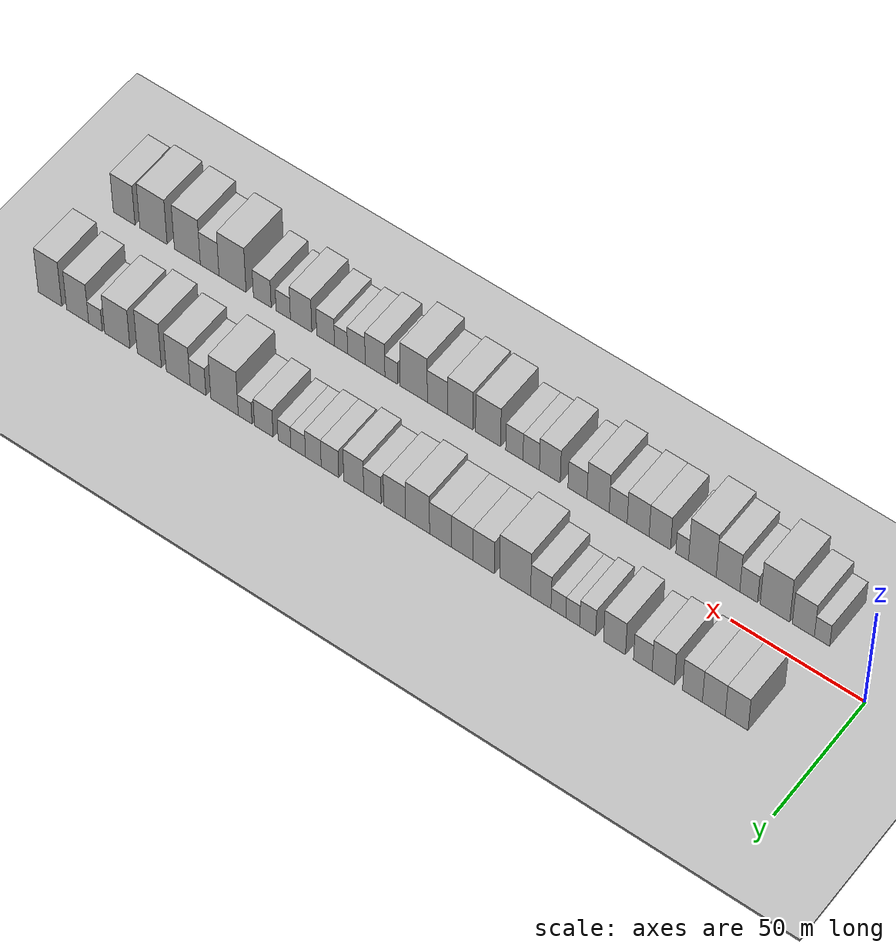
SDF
<?xml version="1.0" encoding="utf-8"?>

<sdf version="1.6">

   <world name="default">

      <gui fullscreen="0">

         <camera name="user_camera">

            <pose>-15 0 4.57585 0 0 0</pose>

            <view_controller>orbit</view_controller>

         </camera>

      </gui>

      <scene>

         <sky>

           <clouds>

             <speed>12</speed>

           </clouds>

         </sky>

         <ambient>0.4 0.4 0.4 1</ambient>

         <background>0.7 0.7 0.7 1</background>

         <shadows>1</shadows>

      </scene>

      <gravity>0 0 -9.8066</gravity>

      <magnetic_field>6e-06 2.3e-05 -4.2e-05</magnetic_field>

      <physics default="0" name="default_physics" type="ode">

         <ode>

            <solver>

               <type>quick</type>

               <iters>10</iters>

               <sor>1.0</sor>

               <use_dynamic_moi_rescaling>0</use_dynamic_moi_rescaling>

            </solver>

            <constraints>

               <cfm>0</cfm>

               <erp>0.2</erp>

               <contact_max_correcting_vel>100</contact_max_correcting_vel>

               <contact_surface_layer>0.001</contact_surface_layer>

            </constraints>

         </ode>

         <max_step_size>0.004</max_step_size>

         <real_time_factor>1</real_time_factor>

         <real_time_update_rate>250</real_time_update_rate>

      </physics>

      <light name="sun" type="directional">

         <cast_shadows>1</cast_shadows>

         <pose>0 0 10 0 0 0</pose>

         <diffuse>0.8 0.8 0.8 1</diffuse>

         <specular>0.2 0.2 0.2 1</specular>

         <attenuation>

            <range>1000</range>

            <constant>0.9</constant>

            <linear>0.01</linear>

            <quadratic>0.001</quadratic>

         </attenuation>

         <direction>-0.5 0.1 -0.9</direction>

      </light>

      <include>

         <name>ground_plane_1</name>

         <uri>model://HANNAS_ground_plane</uri>

         <pose>0 0 0  0 0 0</pose>

      </include>

      <include>

         <name>ground_plane_2</name>

         <uri>model://HANNAS_ground_plane</uri>

         <pose>100 0 0  0 0 0</pose>

      </include>

      <model name="building_1">

         <static>1</static>

         <pose frame="">27.2132 20.0000 0 0.000000 0.000000 1.570796</pose>

         <link name="link">

            <pose frame="">0 0 9.00 0 0 0</pose>

            <collision name="collision">

               <geometry>

                  <box>

                     <size>20.0000 8.4265 18.0000</size>

                  </box>

               </geometry>

               <max_contacts>10</max_contacts>

               <surface>

                  <contact>

                     <ode/>

                  </contact>

                  <bounce/>

                  <friction>

                     <torsional>

                        <ode/>

                     </torsional>

                     <ode/>

                  </friction>

               </surface>

            </collision>

            <visual name="visual">

               <cast_shadows>0</cast_shadows>

               <geometry>

                  <box>

                     <size>20.0000 8.4265 18.0000</size>

                  </box>

               </geometry>

               <material>

                  <script>

                     <uri>model://HANNAS_wall/materials/scripts</uri>

                     <uri>model://HANNAS_wall/materials/textures</uri>

                     <name>vrc/HANNAS_wall</name>

                  </script>

               </material>

            </visual>

            <self_collide>0</self_collide>

            <enable_wind>0</enable_wind>

            <kinematic>0</kinematic>

         </link>

      </model>

      <model name="building_2">

         <static>1</static>

         <pose frame="">35.6799 20.0000 0 0.000000 0.000000 1.570796</pose>

         <link name="link">

            <pose frame="">0 0 9.00 0 0 0</pose>

            <collision name="collision">

               <geometry>

                  <box>

                     <size>20.0000 8.5069 18.0000</size>

                  </box>

               </geometry>

               <max_contacts>10</max_contacts>

               <surface>

                  <contact>

                     <ode/>

                  </contact>

                  <bounce/>

                  <friction>

                     <torsional>

                        <ode/>

                     </torsional>

                     <ode/>

                  </friction>

               </surface>

            </collision>

            <visual name="visual">

               <cast_shadows>0</cast_shadows>

               <geometry>

                  <box>

                     <size>20.0000 8.5069 18.0000</size>

                  </box>

               </geometry>

               <material>

                  <script>

                     <uri>model://HANNAS_wall/materials/scripts</uri>

                     <uri>model://HANNAS_wall/materials/textures</uri>

                     <name>vrc/HANNAS_wall</name>

                  </script>

               </material>

            </visual>

            <self_collide>0</self_collide>

            <enable_wind>0</enable_wind>

            <kinematic>0</kinematic>

         </link>

      </model>

      <model name="building_3">

         <static>1</static>

         <pose frame="">43.6519 20.0000 0 0.000000 0.000000 1.570796</pose>

         <link name="link">

            <pose frame="">0 0 9.00 0 0 0</pose>

            <collision name="collision">

               <geometry>

                  <box>

                     <size>20.0000 7.4371 18.0000</size>

                  </box>

               </geometry>

               <max_contacts>10</max_contacts>

               <surface>

                  <contact>

                     <ode/>

                  </contact>

                  <bounce/>

                  <friction>

                     <torsional>

                        <ode/>

                     </torsional>

                     <ode/>

                  </friction>

               </surface>

            </collision>

            <visual name="visual">

               <cast_shadows>0</cast_shadows>

               <geometry>

                  <box>

                     <size>20.0000 7.4371 18.0000</size>

                  </box>

               </geometry>

               <material>

                  <script>

                     <uri>model://HANNAS_wall/materials/scripts</uri>

                     <uri>model://HANNAS_wall/materials/textures</uri>

                     <name>vrc/HANNAS_wall</name>

                  </script>

               </material>

            </visual>

            <self_collide>0</self_collide>

            <enable_wind>0</enable_wind>

            <kinematic>0</kinematic>

         </link>

      </model>

      <model name="building_4">

         <static>1</static>

         <pose frame="">54.5513 20.0000 0 0.000000 0.000000 1.570796</pose>

         <link name="link">

            <pose frame="">0 0 9.00 0 0 0</pose>

            <collision name="collision">

               <geometry>

                  <box>

                     <size>20.0000 8.3616 18.0000</size>

                  </box>

               </geometry>

               <max_contacts>10</max_contacts>

               <surface>

                  <contact>

                     <ode/>

                  </contact>

                  <bounce/>

                  <friction>

                     <torsional>

                        <ode/>

                     </torsional>

                     <ode/>

                  </friction>

               </surface>

            </collision>

            <visual name="visual">

               <cast_shadows>0</cast_shadows>

               <geometry>

                  <box>

                     <size>20.0000 8.3616 18.0000</size>

                  </box>

               </geometry>

               <material>

                  <script>

                     <uri>model://HANNAS_wall/materials/scripts</uri>

                     <uri>model://HANNAS_wall/materials/textures</uri>

                     <name>vrc/HANNAS_wall</name>

                  </script>

               </material>

            </visual>

            <self_collide>0</self_collide>

            <enable_wind>0</enable_wind>

            <kinematic>0</kinematic>

         </link>

      </model>

      <model name="building_5">

         <static>1</static>

         <pose frame="">62.2326 20.0000 0 0.000000 0.000000 1.570796</pose>

         <link name="link">

            <pose frame="">0 0 7.50 0 0 0</pose>

            <collision name="collision">

               <geometry>

                  <box>

                     <size>20.0000 7.0010 15.0000</size>

                  </box>

               </geometry>

               <max_contacts>10</max_contacts>

               <surface>

                  <contact>

                     <ode/>

                  </contact>

                  <bounce/>

                  <friction>

                     <torsional>

                        <ode/>

                     </torsional>

                     <ode/>

                  </friction>

               </surface>

            </collision>

            <visual name="visual">

               <cast_shadows>0</cast_shadows>

               <geometry>

                  <box>

                     <size>20.0000 7.0010 15.0000</size>

                  </box>

               </geometry>

               <material>

                  <script>

                     <uri>model://HANNAS_wall/materials/scripts</uri>

                     <uri>model://HANNAS_wall/materials/textures</uri>

                     <name>vrc/HANNAS_wall</name>

                  </script>

               </material>

            </visual>

            <self_collide>0</self_collide>

            <enable_wind>0</enable_wind>

            <kinematic>0</kinematic>

         </link>

      </model>

      <model name="building_6">

         <static>1</static>

         <pose frame="">72.8864 20.0000 0 0.000000 0.000000 1.570796</pose>

         <link name="link">

            <pose frame="">0 0 9.00 0 0 0</pose>

            <collision name="collision">

               <geometry>

                  <box>

                     <size>20.0000 8.3066 18.0000</size>

                  </box>

               </geometry>

               <max_contacts>10</max_contacts>

               <surface>

                  <contact>

                     <ode/>

                  </contact>

                  <bounce/>

                  <friction>

                     <torsional>

                        <ode/>

                     </torsional>

                     <ode/>

                  </friction>

               </surface>

            </collision>

            <visual name="visual">

               <cast_shadows>0</cast_shadows>

               <geometry>

                  <box>

                     <size>20.0000 8.3066 18.0000</size>

                  </box>

               </geometry>

               <material>

                  <script>

                     <uri>model://HANNAS_wall/materials/scripts</uri>

                     <uri>model://HANNAS_wall/materials/textures</uri>

                     <name>vrc/HANNAS_wall</name>

                  </script>

               </material>

            </visual>

            <self_collide>0</self_collide>

            <enable_wind>0</enable_wind>

            <kinematic>0</kinematic>

         </link>

      </model>

      <model name="building_7">

         <static>1</static>

         <pose frame="">83.0780 20.0000 0 0.000000 0.000000 1.570796</pose>

         <link name="link">

            <pose frame="">0 0 7.50 0 0 0</pose>

            <collision name="collision">

               <geometry>

                  <box>

                     <size>20.0000 6.0766 15.0000</size>

                  </box>

               </geometry>

               <max_contacts>10</max_contacts>

               <surface>

                  <contact>

                     <ode/>

                  </contact>

                  <bounce/>

                  <friction>

                     <torsional>

                        <ode/>

                     </torsional>

                     <ode/>

                  </friction>

               </surface>

            </collision>

            <visual name="visual">

               <cast_shadows>0</cast_shadows>

               <geometry>

                  <box>

                     <size>20.0000 6.0766 15.0000</size>

                  </box>

               </geometry>

               <material>

                  <script>

                     <uri>model://HANNAS_wall/materials/scripts</uri>

                     <uri>model://HANNAS_wall/materials/textures</uri>

                     <name>vrc/HANNAS_wall</name>

                  </script>

               </material>

            </visual>

            <self_collide>0</self_collide>

            <enable_wind>0</enable_wind>

            <kinematic>0</kinematic>

         </link>

      </model>

      <model name="building_8">

         <static>1</static>

         <pose frame="">88.7378 20.0000 0 0.000000 0.000000 1.570796</pose>

         <link name="link">

            <pose frame="">0 0 6.00 0 0 0</pose>

            <collision name="collision">

               <geometry>

                  <box>

                     <size>20.0000 5.2429 12.0000</size>

                  </box>

               </geometry>

               <max_contacts>10</max_contacts>

               <surface>

                  <contact>

                     <ode/>

                  </contact>

                  <bounce/>

                  <friction>

                     <torsional>

                        <ode/>

                     </torsional>

                     <ode/>

                  </friction>

               </surface>

            </collision>

            <visual name="visual">

               <cast_shadows>0</cast_shadows>

               <geometry>

                  <box>

                     <size>20.0000 5.2429 12.0000</size>

                  </box>

               </geometry>

               <material>

                  <script>

                     <uri>model://HANNAS_wall/materials/scripts</uri>

                     <uri>model://HANNAS_wall/materials/textures</uri>

                     <name>vrc/HANNAS_wall</name>

                  </script>

               </material>

            </visual>

            <self_collide>0</self_collide>

            <enable_wind>0</enable_wind>

            <kinematic>0</kinematic>

         </link>

      </model>

      <model name="building_9">

         <static>1</static>

         <pose frame="">94.1825 20.0000 0 0.000000 0.000000 1.570796</pose>

         <link name="link">

            <pose frame="">0 0 6.00 0 0 0</pose>

            <collision name="collision">

               <geometry>

                  <box>

                     <size>20.0000 5.6465 12.0000</size>

                  </box>

               </geometry>

               <max_contacts>10</max_contacts>

               <surface>

                  <contact>

                     <ode/>

                  </contact>

                  <bounce/>

                  <friction>

                     <torsional>

                        <ode/>

                     </torsional>

                     <ode/>

                  </friction>

               </surface>

            </collision>

            <visual name="visual">

               <cast_shadows>0</cast_shadows>

               <geometry>

                  <box>

                     <size>20.0000 5.6465 12.0000</size>

                  </box>

               </geometry>

               <material>

                  <script>

                     <uri>model://HANNAS_wall/materials/scripts</uri>

                     <uri>model://HANNAS_wall/materials/textures</uri>

                     <name>vrc/HANNAS_wall</name>

                  </script>

               </material>

            </visual>

            <self_collide>0</self_collide>

            <enable_wind>0</enable_wind>

            <kinematic>0</kinematic>

         </link>

      </model>

      <model name="building_10">

         <static>1</static>

         <pose frame="">100.9108 20.0000 0 0.000000 0.000000 1.570796</pose>

         <link name="link">

            <pose frame="">0 0 9.00 0 0 0</pose>

            <collision name="collision">

               <geometry>

                  <box>

                     <size>20.0000 7.8101 18.0000</size>

                  </box>

               </geometry>

               <max_contacts>10</max_contacts>

               <surface>

                  <contact>

                     <ode/>

                  </contact>

                  <bounce/>

                  <friction>

                     <torsional>

                        <ode/>

                     </torsional>

                     <ode/>

                  </friction>

               </surface>

            </collision>

            <visual name="visual">

               <cast_shadows>0</cast_shadows>

               <geometry>

                  <box>

                     <size>20.0000 7.8101 18.0000</size>

                  </box>

               </geometry>

               <material>

                  <script>

                     <uri>model://HANNAS_wall/materials/scripts</uri>

                     <uri>model://HANNAS_wall/materials/textures</uri>

                     <name>vrc/HANNAS_wall</name>

                  </script>

               </material>

            </visual>

            <self_collide>0</self_collide>

            <enable_wind>0</enable_wind>

            <kinematic>0</kinematic>

         </link>

      </model>

      <model name="building_11">

         <static>1</static>

         <pose frame="">110.7731 20.0000 0 0.000000 0.000000 1.570796</pose>

         <link name="link">

            <pose frame="">0 0 12.00 0 0 0</pose>

            <collision name="collision">

               <geometry>

                  <box>

                     <size>20.0000 11.9145 24.0000</size>

                  </box>

               </geometry>

               <max_contacts>10</max_contacts>

               <surface>

                  <contact>

                     <ode/>

                  </contact>

                  <bounce/>

                  <friction>

                     <torsional>

                        <ode/>

                     </torsional>

                     <ode/>

                  </friction>

               </surface>

            </collision>

            <visual name="visual">

               <cast_shadows>0</cast_shadows>

               <geometry>

                  <box>

                     <size>20.0000 11.9145 24.0000</size>

                  </box>

               </geometry>

               <material>

                  <script>

                     <uri>model://HANNAS_wall/materials/scripts</uri>

                     <uri>model://HANNAS_wall/materials/textures</uri>

                     <name>vrc/HANNAS_wall</name>

                  </script>

               </material>

            </visual>

            <self_collide>0</self_collide>

            <enable_wind>0</enable_wind>

            <kinematic>0</kinematic>

         </link>

      </model>

      <model name="building_12">

         <static>1</static>

         <pose frame="">122.9325 20.0000 0 0.000000 0.000000 1.570796</pose>

         <link name="link">

            <pose frame="">0 0 9.00 0 0 0</pose>

            <collision name="collision">

               <geometry>

                  <box>

                     <size>20.0000 8.4043 18.0000</size>

                  </box>

               </geometry>

               <max_contacts>10</max_contacts>

               <surface>

                  <contact>

                     <ode/>

                  </contact>

                  <bounce/>

                  <friction>

                     <torsional>

                        <ode/>

                     </torsional>

                     <ode/>

                  </friction>

               </surface>

            </collision>

            <visual name="visual">

               <cast_shadows>0</cast_shadows>

               <geometry>

                  <box>

                     <size>20.0000 8.4043 18.0000</size>

                  </box>

               </geometry>

               <material>

                  <script>

                     <uri>model://HANNAS_wall/materials/scripts</uri>

                     <uri>model://HANNAS_wall/materials/textures</uri>

                     <name>vrc/HANNAS_wall</name>

                  </script>

               </material>

            </visual>

            <self_collide>0</self_collide>

            <enable_wind>0</enable_wind>

            <kinematic>0</kinematic>

         </link>

      </model>

      <model name="building_13">

         <static>1</static>

         <pose frame="">131.1929 20.0000 0 0.000000 0.000000 1.570796</pose>

         <link name="link">

            <pose frame="">0 0 9.00 0 0 0</pose>

            <collision name="collision">

               <geometry>

                  <box>

                     <size>20.0000 8.1164 18.0000</size>

                  </box>

               </geometry>

               <max_contacts>10</max_contacts>

               <surface>

                  <contact>

                     <ode/>

                  </contact>

                  <bounce/>

                  <friction>

                     <torsional>

                        <ode/>

                     </torsional>

                     <ode/>

                  </friction>

               </surface>

            </collision>

            <visual name="visual">

               <cast_shadows>0</cast_shadows>

               <geometry>

                  <box>

                     <size>20.0000 8.1164 18.0000</size>

                  </box>

               </geometry>

               <material>

                  <script>

                     <uri>model://HANNAS_wall/materials/scripts</uri>

                     <uri>model://HANNAS_wall/materials/textures</uri>

                     <name>vrc/HANNAS_wall</name>

                  </script>

               </material>

            </visual>

            <self_collide>0</self_collide>

            <enable_wind>0</enable_wind>

            <kinematic>0</kinematic>

         </link>

      </model>

      <model name="building_14">

         <static>1</static>

         <pose frame="">139.5708 20.0000 0 0.000000 0.000000 1.570796</pose>

         <link name="link">

            <pose frame="">0 0 9.00 0 0 0</pose>

            <collision name="collision">

               <geometry>

                  <box>

                     <size>20.0000 8.6395 18.0000</size>

                  </box>

               </geometry>

               <max_contacts>10</max_contacts>

               <surface>

                  <contact>

                     <ode/>

                  </contact>

                  <bounce/>

                  <friction>

                     <torsional>

                        <ode/>

                     </torsional>

                     <ode/>

                  </friction>

               </surface>

            </collision>

            <visual name="visual">

               <cast_shadows>0</cast_shadows>

               <geometry>

                  <box>

                     <size>20.0000 8.6395 18.0000</size>

                  </box>

               </geometry>

               <material>

                  <script>

                     <uri>model://HANNAS_wall/materials/scripts</uri>

                     <uri>model://HANNAS_wall/materials/textures</uri>

                     <name>vrc/HANNAS_wall</name>

                  </script>

               </material>

            </visual>

            <self_collide>0</self_collide>

            <enable_wind>0</enable_wind>

            <kinematic>0</kinematic>

         </link>

      </model>

      <model name="building_15">

         <static>1</static>

         <pose frame="">148.5875 20.0000 0 0.000000 0.000000 1.570796</pose>

         <link name="link">

            <pose frame="">0 0 10.50 0 0 0</pose>

            <collision name="collision">

               <geometry>

                  <box>

                     <size>20.0000 9.3938 21.0000</size>

                  </box>

               </geometry>

               <max_contacts>10</max_contacts>

               <surface>

                  <contact>

                     <ode/>

                  </contact>

                  <bounce/>

                  <friction>

                     <torsional>

                        <ode/>

                     </torsional>

                     <ode/>

                  </friction>

               </surface>

            </collision>

            <visual name="visual">

               <cast_shadows>0</cast_shadows>

               <geometry>

                  <box>

                     <size>20.0000 9.3938 21.0000</size>

                  </box>

               </geometry>

               <material>

                  <script>

                     <uri>model://HANNAS_wall/materials/scripts</uri>

                     <uri>model://HANNAS_wall/materials/textures</uri>

                     <name>vrc/HANNAS_wall</name>

                  </script>

               </material>

            </visual>

            <self_collide>0</self_collide>

            <enable_wind>0</enable_wind>

            <kinematic>0</kinematic>

         </link>

      </model>

      <model name="building_16">

         <static>1</static>

         <pose frame="">157.5743 20.0000 0 0.000000 0.000000 1.570796</pose>

         <link name="link">

            <pose frame="">0 0 9.00 0 0 0</pose>

            <collision name="collision">

               <geometry>

                  <box>

                     <size>20.0000 8.5798 18.0000</size>

                  </box>

               </geometry>

               <max_contacts>10</max_contacts>

               <surface>

                  <contact>

                     <ode/>

                  </contact>

                  <bounce/>

                  <friction>

                     <torsional>

                        <ode/>

                     </torsional>

                     <ode/>

                  </friction>

               </surface>

            </collision>

            <visual name="visual">

               <cast_shadows>0</cast_shadows>

               <geometry>

                  <box>

                     <size>20.0000 8.5798 18.0000</size>

                  </box>

               </geometry>

               <material>

                  <script>

                     <uri>model://HANNAS_wall/materials/scripts</uri>

                     <uri>model://HANNAS_wall/materials/textures</uri>

                     <name>vrc/HANNAS_wall</name>

                  </script>

               </material>

            </visual>

            <self_collide>0</self_collide>

            <enable_wind>0</enable_wind>

            <kinematic>0</kinematic>

         </link>

      </model>

      <model name="building_17">

         <static>1</static>

         <pose frame="">166.3001 20.0000 0 0.000000 0.000000 1.570796</pose>

         <link name="link">

            <pose frame="">0 0 7.50 0 0 0</pose>

            <collision name="collision">

               <geometry>

                  <box>

                     <size>20.0000 6.8718 15.0000</size>

                  </box>

               </geometry>

               <max_contacts>10</max_contacts>

               <surface>

                  <contact>

                     <ode/>

                  </contact>

                  <bounce/>

                  <friction>

                     <torsional>

                        <ode/>

                     </torsional>

                     <ode/>

                  </friction>

               </surface>

            </collision>

            <visual name="visual">

               <cast_shadows>0</cast_shadows>

               <geometry>

                  <box>

                     <size>20.0000 6.8718 15.0000</size>

                  </box>

               </geometry>

               <material>

                  <script>

                     <uri>model://HANNAS_wall/materials/scripts</uri>

                     <uri>model://HANNAS_wall/materials/textures</uri>

                     <name>vrc/HANNAS_wall</name>

                  </script>

               </material>

            </visual>

            <self_collide>0</self_collide>

            <enable_wind>0</enable_wind>

            <kinematic>0</kinematic>

         </link>

      </model>

      <model name="building_18">

         <static>1</static>

         <pose frame="">173.6756 20.0000 0 0.000000 0.000000 1.570796</pose>

         <link name="link">

            <pose frame="">0 0 9.00 0 0 0</pose>

            <collision name="collision">

               <geometry>

                  <box>

                     <size>20.0000 7.8792 18.0000</size>

                  </box>

               </geometry>

               <max_contacts>10</max_contacts>

               <surface>

                  <contact>

                     <ode/>

                  </contact>

                  <bounce/>

                  <friction>

                     <torsional>

                        <ode/>

                     </torsional>

                     <ode/>

                  </friction>

               </surface>

            </collision>

            <visual name="visual">

               <cast_shadows>0</cast_shadows>

               <geometry>

                  <box>

                     <size>20.0000 7.8792 18.0000</size>

                  </box>

               </geometry>

               <material>

                  <script>

                     <uri>model://HANNAS_wall/materials/scripts</uri>

                     <uri>model://HANNAS_wall/materials/textures</uri>

                     <name>vrc/HANNAS_wall</name>

                  </script>

               </material>

            </visual>

            <self_collide>0</self_collide>

            <enable_wind>0</enable_wind>

            <kinematic>0</kinematic>

         </link>

      </model>

      <model name="building_19">

         <static>1</static>

         <pose frame="">183.0919 20.0000 0 0.000000 0.000000 1.570796</pose>

         <link name="link">

            <pose frame="">0 0 7.50 0 0 0</pose>

            <collision name="collision">

               <geometry>

                  <box>

                     <size>20.0000 6.9536 15.0000</size>

                  </box>

               </geometry>

               <max_contacts>10</max_contacts>

               <surface>

                  <contact>

                     <ode/>

                  </contact>

                  <bounce/>

                  <friction>

                     <torsional>

                        <ode/>

                     </torsional>

                     <ode/>

                  </friction>

               </surface>

            </collision>

            <visual name="visual">

               <cast_shadows>0</cast_shadows>

               <geometry>

                  <box>

                     <size>20.0000 6.9536 15.0000</size>

                  </box>

               </geometry>

               <material>

                  <script>

                     <uri>model://HANNAS_wall/materials/scripts</uri>

                     <uri>model://HANNAS_wall/materials/textures</uri>

                     <name>vrc/HANNAS_wall</name>

                  </script>

               </material>

            </visual>

            <self_collide>0</self_collide>

            <enable_wind>0</enable_wind>

            <kinematic>0</kinematic>

         </link>

      </model>

      <model name="building_20">

         <static>1</static>

         <pose frame="">189.6906 20.0000 0 0.000000 0.000000 1.570796</pose>

         <link name="link">

            <pose frame="">0 0 7.50 0 0 0</pose>

            <collision name="collision">

               <geometry>

                  <box>

                     <size>20.0000 6.2437 15.0000</size>

                  </box>

               </geometry>

               <max_contacts>10</max_contacts>

               <surface>

                  <contact>

                     <ode/>

                  </contact>

                  <bounce/>

                  <friction>

                     <torsional>

                        <ode/>

                     </torsional>

                     <ode/>

                  </friction>

               </surface>

            </collision>

            <visual name="visual">

               <cast_shadows>0</cast_shadows>

               <geometry>

                  <box>

                     <size>20.0000 6.2437 15.0000</size>

                  </box>

               </geometry>

               <material>

                  <script>

                     <uri>model://HANNAS_wall/materials/scripts</uri>

                     <uri>model://HANNAS_wall/materials/textures</uri>

                     <name>vrc/HANNAS_wall</name>

                  </script>

               </material>

            </visual>

            <self_collide>0</self_collide>

            <enable_wind>0</enable_wind>

            <kinematic>0</kinematic>

         </link>

      </model>

      <model name="building_21">

         <static>1</static>

         <pose frame="">195.7336 20.0000 0 0.000000 0.000000 1.570796</pose>

         <link name="link">

            <pose frame="">0 0 6.00 0 0 0</pose>

            <collision name="collision">

               <geometry>

                  <box>

                     <size>20.0000 5.8425 12.0000</size>

                  </box>

               </geometry>

               <max_contacts>10</max_contacts>

               <surface>

                  <contact>

                     <ode/>

                  </contact>

                  <bounce/>

                  <friction>

                     <torsional>

                        <ode/>

                     </torsional>

                     <ode/>

                  </friction>

               </surface>

            </collision>

            <visual name="visual">

               <cast_shadows>0</cast_shadows>

               <geometry>

                  <box>

                     <size>20.0000 5.8425 12.0000</size>

                  </box>

               </geometry>

               <material>

                  <script>

                     <uri>model://HANNAS_wall/materials/scripts</uri>

                     <uri>model://HANNAS_wall/materials/textures</uri>

                     <name>vrc/HANNAS_wall</name>

                  </script>

               </material>

            </visual>

            <self_collide>0</self_collide>

            <enable_wind>0</enable_wind>

            <kinematic>0</kinematic>

         </link>

      </model>

      <model name="building_22">

         <static>1</static>

         <pose frame="">201.2205 20.0000 0 0.000000 0.000000 1.570796</pose>

         <link name="link">

            <pose frame="">0 0 6.00 0 0 0</pose>

            <collision name="collision">

               <geometry>

                  <box>

                     <size>20.0000 5.1312 12.0000</size>

                  </box>

               </geometry>

               <max_contacts>10</max_contacts>

               <surface>

                  <contact>

                     <ode/>

                  </contact>

                  <bounce/>

                  <friction>

                     <torsional>

                        <ode/>

                     </torsional>

                     <ode/>

                  </friction>

               </surface>

            </collision>

            <visual name="visual">

               <cast_shadows>0</cast_shadows>

               <geometry>

                  <box>

                     <size>20.0000 5.1312 12.0000</size>

                  </box>

               </geometry>

               <material>

                  <script>

                     <uri>model://HANNAS_wall/materials/scripts</uri>

                     <uri>model://HANNAS_wall/materials/textures</uri>

                     <name>vrc/HANNAS_wall</name>

                  </script>

               </material>

            </visual>

            <self_collide>0</self_collide>

            <enable_wind>0</enable_wind>

            <kinematic>0</kinematic>

         </link>

      </model>

      <model name="building_23">

         <static>1</static>

         <pose frame="">209.5263 20.0000 0 0.000000 0.000000 1.570796</pose>

         <link name="link">

            <pose frame="">0 0 7.50 0 0 0</pose>

            <collision name="collision">

               <geometry>

                  <box>

                     <size>20.0000 7.4806 15.0000</size>

                  </box>

               </geometry>

               <max_contacts>10</max_contacts>

               <surface>

                  <contact>

                     <ode/>

                  </contact>

                  <bounce/>

                  <friction>

                     <torsional>

                        <ode/>

                     </torsional>

                     <ode/>

                  </friction>

               </surface>

            </collision>

            <visual name="visual">

               <cast_shadows>0</cast_shadows>

               <geometry>

                  <box>

                     <size>20.0000 7.4806 15.0000</size>

                  </box>

               </geometry>

               <material>

                  <script>

                     <uri>model://HANNAS_wall/materials/scripts</uri>

                     <uri>model://HANNAS_wall/materials/textures</uri>

                     <name>vrc/HANNAS_wall</name>

                  </script>

               </material>

            </visual>

            <self_collide>0</self_collide>

            <enable_wind>0</enable_wind>

            <kinematic>0</kinematic>

         </link>

      </model>

      <model name="building_24">

         <static>1</static>

         <pose frame="">217.0332 20.0000 0 0.000000 0.000000 1.570796</pose>

         <link name="link">

            <pose frame="">0 0 6.00 0 0 0</pose>

            <collision name="collision">

               <geometry>

                  <box>

                     <size>20.0000 5.5331 12.0000</size>

                  </box>

               </geometry>

               <max_contacts>10</max_contacts>

               <surface>

                  <contact>

                     <ode/>

                  </contact>

                  <bounce/>

                  <friction>

                     <torsional>

                        <ode/>

                     </torsional>

                     <ode/>

                  </friction>

               </surface>

            </collision>

            <visual name="visual">

               <cast_shadows>0</cast_shadows>

               <geometry>

                  <box>

                     <size>20.0000 5.5331 12.0000</size>

                  </box>

               </geometry>

               <material>

                  <script>

                     <uri>model://HANNAS_wall/materials/scripts</uri>

                     <uri>model://HANNAS_wall/materials/textures</uri>

                     <name>vrc/HANNAS_wall</name>

                  </script>

               </material>

            </visual>

            <self_collide>0</self_collide>

            <enable_wind>0</enable_wind>

            <kinematic>0</kinematic>

         </link>

      </model>

      <model name="building_25">

         <static>1</static>

         <pose frame="">225.3526 20.0000 0 0.000000 0.000000 1.570796</pose>

         <link name="link">

            <pose frame="">0 0 12.00 0 0 0</pose>

            <collision name="collision">

               <geometry>

                  <box>

                     <size>20.0000 11.1056 24.0000</size>

                  </box>

               </geometry>

               <max_contacts>10</max_contacts>

               <surface>

                  <contact>

                     <ode/>

                  </contact>

                  <bounce/>

                  <friction>

                     <torsional>

                        <ode/>

                     </torsional>

                     <ode/>

                  </friction>

               </surface>

            </collision>

            <visual name="visual">

               <cast_shadows>0</cast_shadows>

               <geometry>

                  <box>

                     <size>20.0000 11.1056 24.0000</size>

                  </box>

               </geometry>

               <material>

                  <script>

                     <uri>model://HANNAS_wall/materials/scripts</uri>

                     <uri>model://HANNAS_wall/materials/textures</uri>

                     <name>vrc/HANNAS_wall</name>

                  </script>

               </material>

            </visual>

            <self_collide>0</self_collide>

            <enable_wind>0</enable_wind>

            <kinematic>0</kinematic>

         </link>

      </model>

      <model name="building_26">

         <static>1</static>

         <pose frame="">236.1133 20.0000 0 0.000000 0.000000 1.570796</pose>

         <link name="link">

            <pose frame="">0 0 7.50 0 0 0</pose>

            <collision name="collision">

               <geometry>

                  <box>

                     <size>20.0000 6.4158 15.0000</size>

                  </box>

               </geometry>

               <max_contacts>10</max_contacts>

               <surface>

                  <contact>

                     <ode/>

                  </contact>

                  <bounce/>

                  <friction>

                     <torsional>

                        <ode/>

                     </torsional>

                     <ode/>

                  </friction>

               </surface>

            </collision>

            <visual name="visual">

               <cast_shadows>0</cast_shadows>

               <geometry>

                  <box>

                     <size>20.0000 6.4158 15.0000</size>

                  </box>

               </geometry>

               <material>

                  <script>

                     <uri>model://HANNAS_wall/materials/scripts</uri>

                     <uri>model://HANNAS_wall/materials/textures</uri>

                     <name>vrc/HANNAS_wall</name>

                  </script>

               </material>

            </visual>

            <self_collide>0</self_collide>

            <enable_wind>0</enable_wind>

            <kinematic>0</kinematic>

         </link>

      </model>

      <model name="building_27">

         <static>1</static>

         <pose frame="">244.1874 20.0000 0 0.000000 0.000000 1.570796</pose>

         <link name="link">

            <pose frame="">0 0 10.50 0 0 0</pose>

            <collision name="collision">

               <geometry>

                  <box>

                     <size>20.0000 9.7324 21.0000</size>

                  </box>

               </geometry>

               <max_contacts>10</max_contacts>

               <surface>

                  <contact>

                     <ode/>

                  </contact>

                  <bounce/>

                  <friction>

                     <torsional>

                        <ode/>

                     </torsional>

                     <ode/>

                  </friction>

               </surface>

            </collision>

            <visual name="visual">

               <cast_shadows>0</cast_shadows>

               <geometry>

                  <box>

                     <size>20.0000 9.7324 21.0000</size>

                  </box>

               </geometry>

               <material>

                  <script>

                     <uri>model://HANNAS_wall/materials/scripts</uri>

                     <uri>model://HANNAS_wall/materials/textures</uri>

                     <name>vrc/HANNAS_wall</name>

                  </script>

               </material>

            </visual>

            <self_collide>0</self_collide>

            <enable_wind>0</enable_wind>

            <kinematic>0</kinematic>

         </link>

      </model>

      <model name="building_28">

         <static>1</static>

         <pose frame="">255.9991 20.0000 0 0.000000 0.000000 1.570796</pose>

         <link name="link">

            <pose frame="">0 0 12.00 0 0 0</pose>

            <collision name="collision">

               <geometry>

                  <box>

                     <size>20.0000 9.8909 24.0000</size>

                  </box>

               </geometry>

               <max_contacts>10</max_contacts>

               <surface>

                  <contact>

                     <ode/>

                  </contact>

                  <bounce/>

                  <friction>

                     <torsional>

                        <ode/>

                     </torsional>

                     <ode/>

                  </friction>

               </surface>

            </collision>

            <visual name="visual">

               <cast_shadows>0</cast_shadows>

               <geometry>

                  <box>

                     <size>20.0000 9.8909 24.0000</size>

                  </box>

               </geometry>

               <material>

                  <script>

                     <uri>model://HANNAS_wall/materials/scripts</uri>

                     <uri>model://HANNAS_wall/materials/textures</uri>

                     <name>vrc/HANNAS_wall</name>

                  </script>

               </material>

            </visual>

            <self_collide>0</self_collide>

            <enable_wind>0</enable_wind>

            <kinematic>0</kinematic>

         </link>

      </model>

      <model name="building_29">

         <static>1</static>

         <pose frame="">269.1668 20.0000 0 0.000000 0.000000 1.570796</pose>

         <link name="link">

            <pose frame="">0 0 10.50 0 0 0</pose>

            <collision name="collision">

               <geometry>

                  <box>

                     <size>20.0000 10.4446 21.0000</size>

                  </box>

               </geometry>

               <max_contacts>10</max_contacts>

               <surface>

                  <contact>

                     <ode/>

                  </contact>

                  <bounce/>

                  <friction>

                     <torsional>

                        <ode/>

                     </torsional>

                     <ode/>

                  </friction>

               </surface>

            </collision>

            <visual name="visual">

               <cast_shadows>0</cast_shadows>

               <geometry>

                  <box>

                     <size>20.0000 10.4446 21.0000</size>

                  </box>

               </geometry>

               <material>

                  <script>

                     <uri>model://HANNAS_wall/materials/scripts</uri>

                     <uri>model://HANNAS_wall/materials/textures</uri>

                     <name>vrc/HANNAS_wall</name>

                  </script>

               </material>

            </visual>

            <self_collide>0</self_collide>

            <enable_wind>0</enable_wind>

            <kinematic>0</kinematic>

         </link>

      </model>

      <model name="building_30">

         <static>1</static>

         <pose frame="">278.2109 20.0000 0 0.000000 0.000000 1.570796</pose>

         <link name="link">

            <pose frame="">0 0 6.00 0 0 0</pose>

            <collision name="collision">

               <geometry>

                  <box>

                     <size>20.0000 5.6436 12.0000</size>

                  </box>

               </geometry>

               <max_contacts>10</max_contacts>

               <surface>

                  <contact>

                     <ode/>

                  </contact>

                  <bounce/>

                  <friction>

                     <torsional>

                        <ode/>

                     </torsional>

                     <ode/>

                  </friction>

               </surface>

            </collision>

            <visual name="visual">

               <cast_shadows>0</cast_shadows>

               <geometry>

                  <box>

                     <size>20.0000 5.6436 12.0000</size>

                  </box>

               </geometry>

               <material>

                  <script>

                     <uri>model://HANNAS_wall/materials/scripts</uri>

                     <uri>model://HANNAS_wall/materials/textures</uri>

                     <name>vrc/HANNAS_wall</name>

                  </script>

               </material>

            </visual>

            <self_collide>0</self_collide>

            <enable_wind>0</enable_wind>

            <kinematic>0</kinematic>

         </link>

      </model>

      <model name="building_31">

         <static>1</static>

         <pose frame="">285.6139 20.0000 0 0.000000 0.000000 1.570796</pose>

         <link name="link">

            <pose frame="">0 0 10.50 0 0 0</pose>

            <collision name="collision">

               <geometry>

                  <box>

                     <size>20.0000 9.1622 21.0000</size>

                  </box>

               </geometry>

               <max_contacts>10</max_contacts>

               <surface>

                  <contact>

                     <ode/>

                  </contact>

                  <bounce/>

                  <friction>

                     <torsional>

                        <ode/>

                     </torsional>

                     <ode/>

                  </friction>

               </surface>

            </collision>

            <visual name="visual">

               <cast_shadows>0</cast_shadows>

               <geometry>

                  <box>

                     <size>20.0000 9.1622 21.0000</size>

                  </box>

               </geometry>

               <material>

                  <script>

                     <uri>model://HANNAS_wall/materials/scripts</uri>

                     <uri>model://HANNAS_wall/materials/textures</uri>

                     <name>vrc/HANNAS_wall</name>

                  </script>

               </material>

            </visual>

            <self_collide>0</self_collide>

            <enable_wind>0</enable_wind>

            <kinematic>0</kinematic>

         </link>

      </model>

      <model name="building_32">

         <static>1</static>

         <pose frame="">297.1153 20.0000 0 0.000000 0.000000 1.570796</pose>

         <link name="link">

            <pose frame="">0 0 12.00 0 0 0</pose>

            <collision name="collision">

               <geometry>

                  <box>

                     <size>20.0000 9.8406 24.0000</size>

                  </box>

               </geometry>

               <max_contacts>10</max_contacts>

               <surface>

                  <contact>

                     <ode/>

                  </contact>

                  <bounce/>

                  <friction>

                     <torsional>

                        <ode/>

                     </torsional>

                     <ode/>

                  </friction>

               </surface>

            </collision>

            <visual name="visual">

               <cast_shadows>0</cast_shadows>

               <geometry>

                  <box>

                     <size>20.0000 9.8406 24.0000</size>

                  </box>

               </geometry>

               <material>

                  <script>

                     <uri>model://HANNAS_wall/materials/scripts</uri>

                     <uri>model://HANNAS_wall/materials/textures</uri>

                     <name>vrc/HANNAS_wall</name>

                  </script>

               </material>

            </visual>

            <self_collide>0</self_collide>

            <enable_wind>0</enable_wind>

            <kinematic>0</kinematic>

         </link>

      </model>

      <model name="building_33">

         <static>1</static>

         <pose frame="">22.8584 -20.0000 0 0.000000 0.000000 1.570796</pose>

         <link name="link">

            <pose frame="">0 0 6.00 0 0 0</pose>

            <collision name="collision">

               <geometry>

                  <box>

                     <size>20.0000 5.7169 12.0000</size>

                  </box>

               </geometry>

               <max_contacts>10</max_contacts>

               <surface>

                  <contact>

                     <ode/>

                  </contact>

                  <bounce/>

                  <friction>

                     <torsional>

                        <ode/>

                     </torsional>

                     <ode/>

                  </friction>

               </surface>

            </collision>

            <visual name="visual">

               <cast_shadows>0</cast_shadows>

               <geometry>

                  <box>

                     <size>20.0000 5.7169 12.0000</size>

                  </box>

               </geometry>

               <material>

                  <script>

                     <uri>model://HANNAS_wall/materials/scripts</uri>

                     <uri>model://HANNAS_wall/materials/textures</uri>

                     <name>vrc/HANNAS_wall</name>

                  </script>

               </material>

            </visual>

            <self_collide>0</self_collide>

            <enable_wind>0</enable_wind>

            <kinematic>0</kinematic>

         </link>

      </model>

      <model name="building_34">

         <static>1</static>

         <pose frame="">29.8054 -20.0000 0 0.000000 0.000000 1.570796</pose>

         <link name="link">

            <pose frame="">0 0 9.00 0 0 0</pose>

            <collision name="collision">

               <geometry>

                  <box>

                     <size>20.0000 8.1771 18.0000</size>

                  </box>

               </geometry>

               <max_contacts>10</max_contacts>

               <surface>

                  <contact>

                     <ode/>

                  </contact>

                  <bounce/>

                  <friction>

                     <torsional>

                        <ode/>

                     </torsional>

                     <ode/>

                  </friction>

               </surface>

            </collision>

            <visual name="visual">

               <cast_shadows>0</cast_shadows>

               <geometry>

                  <box>

                     <size>20.0000 8.1771 18.0000</size>

                  </box>

               </geometry>

               <material>

                  <script>

                     <uri>model://HANNAS_wall/materials/scripts</uri>

                     <uri>model://HANNAS_wall/materials/textures</uri>

                     <name>vrc/HANNAS_wall</name>

                  </script>

               </material>

            </visual>

            <self_collide>0</self_collide>

            <enable_wind>0</enable_wind>

            <kinematic>0</kinematic>

         </link>

      </model>

      <model name="building_35">

         <static>1</static>

         <pose frame="">40.4253 -20.0000 0 0.000000 0.000000 1.570796</pose>

         <link name="link">

            <pose frame="">0 0 12.00 0 0 0</pose>

            <collision name="collision">

               <geometry>

                  <box>

                     <size>20.0000 11.0627 24.0000</size>

                  </box>

               </geometry>

               <max_contacts>10</max_contacts>

               <surface>

                  <contact>

                     <ode/>

                  </contact>

                  <bounce/>

                  <friction>

                     <torsional>

                        <ode/>

                     </torsional>

                     <ode/>

                  </friction>

               </surface>

            </collision>

            <visual name="visual">

               <cast_shadows>0</cast_shadows>

               <geometry>

                  <box>

                     <size>20.0000 11.0627 24.0000</size>

                  </box>

               </geometry>

               <material>

                  <script>

                     <uri>model://HANNAS_wall/materials/scripts</uri>

                     <uri>model://HANNAS_wall/materials/textures</uri>

                     <name>vrc/HANNAS_wall</name>

                  </script>

               </material>

            </visual>

            <self_collide>0</self_collide>

            <enable_wind>0</enable_wind>

            <kinematic>0</kinematic>

         </link>

      </model>

      <model name="building_36">

         <static>1</static>

         <pose frame="">50.2929 -20.0000 0 0.000000 0.000000 1.570796</pose>

         <link name="link">

            <pose frame="">0 0 7.50 0 0 0</pose>

            <collision name="collision">

               <geometry>

                  <box>

                     <size>20.0000 6.6725 15.0000</size>

                  </box>

               </geometry>

               <max_contacts>10</max_contacts>

               <surface>

                  <contact>

                     <ode/>

                  </contact>

                  <bounce/>

                  <friction>

                     <torsional>

                        <ode/>

                     </torsional>

                     <ode/>

                  </friction>

               </surface>

            </collision>

            <visual name="visual">

               <cast_shadows>0</cast_shadows>

               <geometry>

                  <box>

                     <size>20.0000 6.6725 15.0000</size>

                  </box>

               </geometry>

               <material>

                  <script>

                     <uri>model://HANNAS_wall/materials/scripts</uri>

                     <uri>model://HANNAS_wall/materials/textures</uri>

                     <name>vrc/HANNAS_wall</name>

                  </script>

               </material>

            </visual>

            <self_collide>0</self_collide>

            <enable_wind>0</enable_wind>

            <kinematic>0</kinematic>

         </link>

      </model>

      <model name="building_37">

         <static>1</static>

         <pose frame="">58.0925 -20.0000 0 0.000000 0.000000 1.570796</pose>

         <link name="link">

            <pose frame="">0 0 10.50 0 0 0</pose>

            <collision name="collision">

               <geometry>

                  <box>

                     <size>20.0000 8.9267 21.0000</size>

                  </box>

               </geometry>

               <max_contacts>10</max_contacts>

               <surface>

                  <contact>

                     <ode/>

                  </contact>

                  <bounce/>

                  <friction>

                     <torsional>

                        <ode/>

                     </torsional>

                     <ode/>

                  </friction>

               </surface>

            </collision>

            <visual name="visual">

               <cast_shadows>0</cast_shadows>

               <geometry>

                  <box>

                     <size>20.0000 8.9267 21.0000</size>

                  </box>

               </geometry>

               <material>

                  <script>

                     <uri>model://HANNAS_wall/materials/scripts</uri>

                     <uri>model://HANNAS_wall/materials/textures</uri>

                     <name>vrc/HANNAS_wall</name>

                  </script>

               </material>

            </visual>

            <self_collide>0</self_collide>

            <enable_wind>0</enable_wind>

            <kinematic>0</kinematic>

         </link>

      </model>

      <model name="building_38">

         <static>1</static>

         <pose frame="">67.7901 -20.0000 0 0.000000 0.000000 1.570796</pose>

         <link name="link">

            <pose frame="">0 0 12.00 0 0 0</pose>

            <collision name="collision">

               <geometry>

                  <box>

                     <size>20.0000 10.4684 24.0000</size>

                  </box>

               </geometry>

               <max_contacts>10</max_contacts>

               <surface>

                  <contact>

                     <ode/>

                  </contact>

                  <bounce/>

                  <friction>

                     <torsional>

                        <ode/>

                     </torsional>

                     <ode/>

                  </friction>

               </surface>

            </collision>

            <visual name="visual">

               <cast_shadows>0</cast_shadows>

               <geometry>

                  <box>

                     <size>20.0000 10.4684 24.0000</size>

                  </box>

               </geometry>

               <material>

                  <script>

                     <uri>model://HANNAS_wall/materials/scripts</uri>

                     <uri>model://HANNAS_wall/materials/textures</uri>

                     <name>vrc/HANNAS_wall</name>

                  </script>

               </material>

            </visual>

            <self_collide>0</self_collide>

            <enable_wind>0</enable_wind>

            <kinematic>0</kinematic>

         </link>

      </model>

      <model name="building_39">

         <static>1</static>

         <pose frame="">75.4526 -20.0000 0 0.000000 0.000000 1.570796</pose>

         <link name="link">

            <pose frame="">0 0 6.00 0 0 0</pose>

            <collision name="collision">

               <geometry>

                  <box>

                     <size>20.0000 4.8567 12.0000</size>

                  </box>

               </geometry>

               <max_contacts>10</max_contacts>

               <surface>

                  <contact>

                     <ode/>

                  </contact>

                  <bounce/>

                  <friction>

                     <torsional>

                        <ode/>

                     </torsional>

                     <ode/>

                  </friction>

               </surface>

            </collision>

            <visual name="visual">

               <cast_shadows>0</cast_shadows>

               <geometry>

                  <box>

                     <size>20.0000 4.8567 12.0000</size>

                  </box>

               </geometry>

               <material>

                  <script>

                     <uri>model://HANNAS_wall/materials/scripts</uri>

                     <uri>model://HANNAS_wall/materials/textures</uri>

                     <name>vrc/HANNAS_wall</name>

                  </script>

               </material>

            </visual>

            <self_collide>0</self_collide>

            <enable_wind>0</enable_wind>

            <kinematic>0</kinematic>

         </link>

      </model>

      <model name="building_40">

         <static>1</static>

         <pose frame="">83.9626 -20.0000 0 0.000000 0.000000 1.570796</pose>

         <link name="link">

            <pose frame="">0 0 9.00 0 0 0</pose>

            <collision name="collision">

               <geometry>

                  <box>

                     <size>20.0000 8.1632 18.0000</size>

                  </box>

               </geometry>

               <max_contacts>10</max_contacts>

               <surface>

                  <contact>

                     <ode/>

                  </contact>

                  <bounce/>

                  <friction>

                     <torsional>

                        <ode/>

                     </torsional>

                     <ode/>

                  </friction>

               </surface>

            </collision>

            <visual name="visual">

               <cast_shadows>0</cast_shadows>

               <geometry>

                  <box>

                     <size>20.0000 8.1632 18.0000</size>

                  </box>

               </geometry>

               <material>

                  <script>

                     <uri>model://HANNAS_wall/materials/scripts</uri>

                     <uri>model://HANNAS_wall/materials/textures</uri>

                     <name>vrc/HANNAS_wall</name>

                  </script>

               </material>

            </visual>

            <self_collide>0</self_collide>

            <enable_wind>0</enable_wind>

            <kinematic>0</kinematic>

         </link>

      </model>

      <model name="building_41">

         <static>1</static>

         <pose frame="">92.2539 -20.0000 0 0.000000 0.000000 1.570796</pose>

         <link name="link">

            <pose frame="">0 0 9.00 0 0 0</pose>

            <collision name="collision">

               <geometry>

                  <box>

                     <size>20.0000 8.4194 18.0000</size>

                  </box>

               </geometry>

               <max_contacts>10</max_contacts>

               <surface>

                  <contact>

                     <ode/>

                  </contact>

                  <bounce/>

                  <friction>

                     <torsional>

                        <ode/>

                     </torsional>

                     <ode/>

                  </friction>

               </surface>

            </collision>

            <visual name="visual">

               <cast_shadows>0</cast_shadows>

               <geometry>

                  <box>

                     <size>20.0000 8.4194 18.0000</size>

                  </box>

               </geometry>

               <material>

                  <script>

                     <uri>model://HANNAS_wall/materials/scripts</uri>

                     <uri>model://HANNAS_wall/materials/textures</uri>

                     <name>vrc/HANNAS_wall</name>

                  </script>

               </material>

            </visual>

            <self_collide>0</self_collide>

            <enable_wind>0</enable_wind>

            <kinematic>0</kinematic>

         </link>

      </model>

      <model name="building_42">

         <static>1</static>

         <pose frame="">99.9239 -20.0000 0 0.000000 0.000000 1.570796</pose>

         <link name="link">

            <pose frame="">0 0 7.50 0 0 0</pose>

            <collision name="collision">

               <geometry>

                  <box>

                     <size>20.0000 6.9206 15.0000</size>

                  </box>

               </geometry>

               <max_contacts>10</max_contacts>

               <surface>

                  <contact>

                     <ode/>

                  </contact>

                  <bounce/>

                  <friction>

                     <torsional>

                        <ode/>

                     </torsional>

                     <ode/>

                  </friction>

               </surface>

            </collision>

            <visual name="visual">

               <cast_shadows>0</cast_shadows>

               <geometry>

                  <box>

                     <size>20.0000 6.9206 15.0000</size>

                  </box>

               </geometry>

               <material>

                  <script>

                     <uri>model://HANNAS_wall/materials/scripts</uri>

                     <uri>model://HANNAS_wall/materials/textures</uri>

                     <name>vrc/HANNAS_wall</name>

                  </script>

               </material>

            </visual>

            <self_collide>0</self_collide>

            <enable_wind>0</enable_wind>

            <kinematic>0</kinematic>

         </link>

      </model>

      <model name="building_43">

         <static>1</static>

         <pose frame="">107.6660 -20.0000 0 0.000000 0.000000 1.570796</pose>

         <link name="link">

            <pose frame="">0 0 10.50 0 0 0</pose>

            <collision name="collision">

               <geometry>

                  <box>

                     <size>20.0000 8.5636 21.0000</size>

                  </box>

               </geometry>

               <max_contacts>10</max_contacts>

               <surface>

                  <contact>

                     <ode/>

                  </contact>

                  <bounce/>

                  <friction>

                     <torsional>

                        <ode/>

                     </torsional>

                     <ode/>

                  </friction>

               </surface>

            </collision>

            <visual name="visual">

               <cast_shadows>0</cast_shadows>

               <geometry>

                  <box>

                     <size>20.0000 8.5636 21.0000</size>

                  </box>

               </geometry>

               <material>

                  <script>

                     <uri>model://HANNAS_wall/materials/scripts</uri>

                     <uri>model://HANNAS_wall/materials/textures</uri>

                     <name>vrc/HANNAS_wall</name>

                  </script>

               </material>

            </visual>

            <self_collide>0</self_collide>

            <enable_wind>0</enable_wind>

            <kinematic>0</kinematic>

         </link>

      </model>

      <model name="building_44">

         <static>1</static>

         <pose frame="">115.6397 -20.0000 0 0.000000 0.000000 1.570796</pose>

         <link name="link">

            <pose frame="">0 0 7.50 0 0 0</pose>

            <collision name="collision">

               <geometry>

                  <box>

                     <size>20.0000 7.3838 15.0000</size>

                  </box>

               </geometry>

               <max_contacts>10</max_contacts>

               <surface>

                  <contact>

                     <ode/>

                  </contact>

                  <bounce/>

                  <friction>

                     <torsional>

                        <ode/>

                     </torsional>

                     <ode/>

                  </friction>

               </surface>

            </collision>

            <visual name="visual">

               <cast_shadows>0</cast_shadows>

               <geometry>

                  <box>

                     <size>20.0000 7.3838 15.0000</size>

                  </box>

               </geometry>

               <material>

                  <script>

                     <uri>model://HANNAS_wall/materials/scripts</uri>

                     <uri>model://HANNAS_wall/materials/textures</uri>

                     <name>vrc/HANNAS_wall</name>

                  </script>

               </material>

            </visual>

            <self_collide>0</self_collide>

            <enable_wind>0</enable_wind>

            <kinematic>0</kinematic>

         </link>

      </model>

      <model name="building_45">

         <static>1</static>

         <pose frame="">126.3735 -20.0000 0 0.000000 0.000000 1.570796</pose>

         <link name="link">

            <pose frame="">0 0 9.00 0 0 0</pose>

            <collision name="collision">

               <geometry>

                  <box>

                     <size>20.0000 8.0839 18.0000</size>

                  </box>

               </geometry>

               <max_contacts>10</max_contacts>

               <surface>

                  <contact>

                     <ode/>

                  </contact>

                  <bounce/>

                  <friction>

                     <torsional>

                        <ode/>

                     </torsional>

                     <ode/>

                  </friction>

               </surface>

            </collision>

            <visual name="visual">

               <cast_shadows>0</cast_shadows>

               <geometry>

                  <box>

                     <size>20.0000 8.0839 18.0000</size>

                  </box>

               </geometry>

               <material>

                  <script>

                     <uri>model://HANNAS_wall/materials/scripts</uri>

                     <uri>model://HANNAS_wall/materials/textures</uri>

                     <name>vrc/HANNAS_wall</name>

                  </script>

               </material>

            </visual>

            <self_collide>0</self_collide>

            <enable_wind>0</enable_wind>

            <kinematic>0</kinematic>

         </link>

      </model>

      <model name="building_46">

         <static>1</static>

         <pose frame="">133.6228 -20.0000 0 0.000000 0.000000 1.570796</pose>

         <link name="link">

            <pose frame="">0 0 7.50 0 0 0</pose>

            <collision name="collision">

               <geometry>

                  <box>

                     <size>20.0000 6.4146 15.0000</size>

                  </box>

               </geometry>

               <max_contacts>10</max_contacts>

               <surface>

                  <contact>

                     <ode/>

                  </contact>

                  <bounce/>

                  <friction>

                     <torsional>

                        <ode/>

                     </torsional>

                     <ode/>

                  </friction>

               </surface>

            </collision>

            <visual name="visual">

               <cast_shadows>0</cast_shadows>

               <geometry>

                  <box>

                     <size>20.0000 6.4146 15.0000</size>

                  </box>

               </geometry>

               <material>

                  <script>

                     <uri>model://HANNAS_wall/materials/scripts</uri>

                     <uri>model://HANNAS_wall/materials/textures</uri>

                     <name>vrc/HANNAS_wall</name>

                  </script>

               </material>

            </visual>

            <self_collide>0</self_collide>

            <enable_wind>0</enable_wind>

            <kinematic>0</kinematic>

         </link>

      </model>

      <model name="building_47">

         <static>1</static>

         <pose frame="">140.2219 -20.0000 0 0.000000 0.000000 1.570796</pose>

         <link name="link">

            <pose frame="">0 0 7.50 0 0 0</pose>

            <collision name="collision">

               <geometry>

                  <box>

                     <size>20.0000 6.7836 15.0000</size>

                  </box>

               </geometry>

               <max_contacts>10</max_contacts>

               <surface>

                  <contact>

                     <ode/>

                  </contact>

                  <bounce/>

                  <friction>

                     <torsional>

                        <ode/>

                     </torsional>

                     <ode/>

                  </friction>

               </surface>

            </collision>

            <visual name="visual">

               <cast_shadows>0</cast_shadows>

               <geometry>

                  <box>

                     <size>20.0000 6.7836 15.0000</size>

                  </box>

               </geometry>

               <material>

                  <script>

                     <uri>model://HANNAS_wall/materials/scripts</uri>

                     <uri>model://HANNAS_wall/materials/textures</uri>

                     <name>vrc/HANNAS_wall</name>

                  </script>

               </material>

            </visual>

            <self_collide>0</self_collide>

            <enable_wind>0</enable_wind>

            <kinematic>0</kinematic>

         </link>

      </model>

      <model name="building_48">

         <static>1</static>

         <pose frame="">150.5389 -20.0000 0 0.000000 0.000000 1.570796</pose>

         <link name="link">

            <pose frame="">0 0 10.50 0 0 0</pose>

            <collision name="collision">

               <geometry>

                  <box>

                     <size>20.0000 9.8505 21.0000</size>

                  </box>

               </geometry>

               <max_contacts>10</max_contacts>

               <surface>

                  <contact>

                     <ode/>

                  </contact>

                  <bounce/>

                  <friction>

                     <torsional>

                        <ode/>

                     </torsional>

                     <ode/>

                  </friction>

               </surface>

            </collision>

            <visual name="visual">

               <cast_shadows>0</cast_shadows>

               <geometry>

                  <box>

                     <size>20.0000 9.8505 21.0000</size>

                  </box>

               </geometry>

               <material>

                  <script>

                     <uri>model://HANNAS_wall/materials/scripts</uri>

                     <uri>model://HANNAS_wall/materials/textures</uri>

                     <name>vrc/HANNAS_wall</name>

                  </script>

               </material>

            </visual>

            <self_collide>0</self_collide>

            <enable_wind>0</enable_wind>

            <kinematic>0</kinematic>

         </link>

      </model>

      <model name="building_49">

         <static>1</static>

         <pose frame="">161.4462 -20.0000 0 0.000000 0.000000 1.570796</pose>

         <link name="link">

            <pose frame="">0 0 10.50 0 0 0</pose>

            <collision name="collision">

               <geometry>

                  <box>

                     <size>20.0000 9.9641 21.0000</size>

                  </box>

               </geometry>

               <max_contacts>10</max_contacts>

               <surface>

                  <contact>

                     <ode/>

                  </contact>

                  <bounce/>

                  <friction>

                     <torsional>

                        <ode/>

                     </torsional>

                     <ode/>

                  </friction>

               </surface>

            </collision>

            <visual name="visual">

               <cast_shadows>0</cast_shadows>

               <geometry>

                  <box>

                     <size>20.0000 9.9641 21.0000</size>

                  </box>

               </geometry>

               <material>

                  <script>

                     <uri>model://HANNAS_wall/materials/scripts</uri>

                     <uri>model://HANNAS_wall/materials/textures</uri>

                     <name>vrc/HANNAS_wall</name>

                  </script>

               </material>

            </visual>

            <self_collide>0</self_collide>

            <enable_wind>0</enable_wind>

            <kinematic>0</kinematic>

         </link>

      </model>

      <model name="building_50">

         <static>1</static>

         <pose frame="">170.5094 -20.0000 0 0.000000 0.000000 1.570796</pose>

         <link name="link">

            <pose frame="">0 0 9.00 0 0 0</pose>

            <collision name="collision">

               <geometry>

                  <box>

                     <size>20.0000 8.1622 18.0000</size>

                  </box>

               </geometry>

               <max_contacts>10</max_contacts>

               <surface>

                  <contact>

                     <ode/>

                  </contact>

                  <bounce/>

                  <friction>

                     <torsional>

                        <ode/>

                     </torsional>

                     <ode/>

                  </friction>

               </surface>

            </collision>

            <visual name="visual">

               <cast_shadows>0</cast_shadows>

               <geometry>

                  <box>

                     <size>20.0000 8.1622 18.0000</size>

                  </box>

               </geometry>

               <material>

                  <script>

                     <uri>model://HANNAS_wall/materials/scripts</uri>

                     <uri>model://HANNAS_wall/materials/textures</uri>

                     <name>vrc/HANNAS_wall</name>

                  </script>

               </material>

            </visual>

            <self_collide>0</self_collide>

            <enable_wind>0</enable_wind>

            <kinematic>0</kinematic>

         </link>

      </model>

      <model name="building_51">

         <static>1</static>

         <pose frame="">180.0076 -20.0000 0 0.000000 0.000000 1.570796</pose>

         <link name="link">

            <pose frame="">0 0 12.00 0 0 0</pose>

            <collision name="collision">

               <geometry>

                  <box>

                     <size>20.0000 10.8341 24.0000</size>

                  </box>

               </geometry>

               <max_contacts>10</max_contacts>

               <surface>

                  <contact>

                     <ode/>

                  </contact>

                  <bounce/>

                  <friction>

                     <torsional>

                        <ode/>

                     </torsional>

                     <ode/>

                  </friction>

               </surface>

            </collision>

            <visual name="visual">

               <cast_shadows>0</cast_shadows>

               <geometry>

                  <box>

                     <size>20.0000 10.8341 24.0000</size>

                  </box>

               </geometry>

               <material>

                  <script>

                     <uri>model://HANNAS_wall/materials/scripts</uri>

                     <uri>model://HANNAS_wall/materials/textures</uri>

                     <name>vrc/HANNAS_wall</name>

                  </script>

               </material>

            </visual>

            <self_collide>0</self_collide>

            <enable_wind>0</enable_wind>

            <kinematic>0</kinematic>

         </link>

      </model>

      <model name="building_52">

         <static>1</static>

         <pose frame="">188.9619 -20.0000 0 0.000000 0.000000 1.570796</pose>

         <link name="link">

            <pose frame="">0 0 6.00 0 0 0</pose>

            <collision name="collision">

               <geometry>

                  <box>

                     <size>20.0000 5.0745 12.0000</size>

                  </box>

               </geometry>

               <max_contacts>10</max_contacts>

               <surface>

                  <contact>

                     <ode/>

                  </contact>

                  <bounce/>

                  <friction>

                     <torsional>

                        <ode/>

                     </torsional>

                     <ode/>

                  </friction>

               </surface>

            </collision>

            <visual name="visual">

               <cast_shadows>0</cast_shadows>

               <geometry>

                  <box>

                     <size>20.0000 5.0745 12.0000</size>

                  </box>

               </geometry>

               <material>

                  <script>

                     <uri>model://HANNAS_wall/materials/scripts</uri>

                     <uri>model://HANNAS_wall/materials/textures</uri>

                     <name>vrc/HANNAS_wall</name>

                  </script>

               </material>

            </visual>

            <self_collide>0</self_collide>

            <enable_wind>0</enable_wind>

            <kinematic>0</kinematic>

         </link>

      </model>

      <model name="building_53">

         <static>1</static>

         <pose frame="">195.4477 -20.0000 0 0.000000 0.000000 1.570796</pose>

         <link name="link">

            <pose frame="">0 0 9.00 0 0 0</pose>

            <collision name="collision">

               <geometry>

                  <box>

                     <size>20.0000 7.8971 18.0000</size>

                  </box>

               </geometry>

               <max_contacts>10</max_contacts>

               <surface>

                  <contact>

                     <ode/>

                  </contact>

                  <bounce/>

                  <friction>

                     <torsional>

                        <ode/>

                     </torsional>

                     <ode/>

                  </friction>

               </surface>

            </collision>

            <visual name="visual">

               <cast_shadows>0</cast_shadows>

               <geometry>

                  <box>

                     <size>20.0000 7.8971 18.0000</size>

                  </box>

               </geometry>

               <material>

                  <script>

                     <uri>model://HANNAS_wall/materials/scripts</uri>

                     <uri>model://HANNAS_wall/materials/textures</uri>

                     <name>vrc/HANNAS_wall</name>

                  </script>

               </material>

            </visual>

            <self_collide>0</self_collide>

            <enable_wind>0</enable_wind>

            <kinematic>0</kinematic>

         </link>

      </model>

      <model name="building_54">

         <static>1</static>

         <pose frame="">202.9474 -20.0000 0 0.000000 0.000000 1.570796</pose>

         <link name="link">

            <pose frame="">0 0 7.50 0 0 0</pose>

            <collision name="collision">

               <geometry>

                  <box>

                     <size>20.0000 7.1022 15.0000</size>

                  </box>

               </geometry>

               <max_contacts>10</max_contacts>

               <surface>

                  <contact>

                     <ode/>

                  </contact>

                  <bounce/>

                  <friction>

                     <torsional>

                        <ode/>

                     </torsional>

                     <ode/>

                  </friction>

               </surface>

            </collision>

            <visual name="visual">

               <cast_shadows>0</cast_shadows>

               <geometry>

                  <box>

                     <size>20.0000 7.1022 15.0000</size>

                  </box>

               </geometry>

               <material>

                  <script>

                     <uri>model://HANNAS_wall/materials/scripts</uri>

                     <uri>model://HANNAS_wall/materials/textures</uri>

                     <name>vrc/HANNAS_wall</name>

                  </script>

               </material>

            </visual>

            <self_collide>0</self_collide>

            <enable_wind>0</enable_wind>

            <kinematic>0</kinematic>

         </link>

      </model>

      <model name="building_55">

         <static>1</static>

         <pose frame="">209.1400 -20.0000 0 0.000000 0.000000 1.570796</pose>

         <link name="link">

            <pose frame="">0 0 6.00 0 0 0</pose>

            <collision name="collision">

               <geometry>

                  <box>

                     <size>20.0000 5.2831 12.0000</size>

                  </box>

               </geometry>

               <max_contacts>10</max_contacts>

               <surface>

                  <contact>

                     <ode/>

                  </contact>

                  <bounce/>

                  <friction>

                     <torsional>

                        <ode/>

                     </torsional>

                     <ode/>

                  </friction>

               </surface>

            </collision>

            <visual name="visual">

               <cast_shadows>0</cast_shadows>

               <geometry>

                  <box>

                     <size>20.0000 5.2831 12.0000</size>

                  </box>

               </geometry>

               <material>

                  <script>

                     <uri>model://HANNAS_wall/materials/scripts</uri>

                     <uri>model://HANNAS_wall/materials/textures</uri>

                     <name>vrc/HANNAS_wall</name>

                  </script>

               </material>

            </visual>

            <self_collide>0</self_collide>

            <enable_wind>0</enable_wind>

            <kinematic>0</kinematic>

         </link>

      </model>

      <model name="building_56">

         <static>1</static>

         <pose frame="">215.3813 -20.0000 0 0.000000 0.000000 1.570796</pose>

         <link name="link">

            <pose frame="">0 0 7.50 0 0 0</pose>

            <collision name="collision">

               <geometry>

                  <box>

                     <size>20.0000 7.1994 15.0000</size>

                  </box>

               </geometry>

               <max_contacts>10</max_contacts>

               <surface>

                  <contact>

                     <ode/>

                  </contact>

                  <bounce/>

                  <friction>

                     <torsional>

                        <ode/>

                     </torsional>

                     <ode/>

                  </friction>

               </surface>

            </collision>

            <visual name="visual">

               <cast_shadows>0</cast_shadows>

               <geometry>

                  <box>

                     <size>20.0000 7.1994 15.0000</size>

                  </box>

               </geometry>

               <material>

                  <script>

                     <uri>model://HANNAS_wall/materials/scripts</uri>

                     <uri>model://HANNAS_wall/materials/textures</uri>

                     <name>vrc/HANNAS_wall</name>

                  </script>

               </material>

            </visual>

            <self_collide>0</self_collide>

            <enable_wind>0</enable_wind>

            <kinematic>0</kinematic>

         </link>

      </model>

      <model name="building_57">

         <static>1</static>

         <pose frame="">225.3347 -20.0000 0 0.000000 0.000000 1.570796</pose>

         <link name="link">

            <pose frame="">0 0 9.00 0 0 0</pose>

            <collision name="collision">

               <geometry>

                  <box>

                     <size>20.0000 8.7075 18.0000</size>

                  </box>

               </geometry>

               <max_contacts>10</max_contacts>

               <surface>

                  <contact>

                     <ode/>

                  </contact>

                  <bounce/>

                  <friction>

                     <torsional>

                        <ode/>

                     </torsional>

                     <ode/>

                  </friction>

               </surface>

            </collision>

            <visual name="visual">

               <cast_shadows>0</cast_shadows>

               <geometry>

                  <box>

                     <size>20.0000 8.7075 18.0000</size>

                  </box>

               </geometry>

               <material>

                  <script>

                     <uri>model://HANNAS_wall/materials/scripts</uri>

                     <uri>model://HANNAS_wall/materials/textures</uri>

                     <name>vrc/HANNAS_wall</name>

                  </script>

               </material>

            </visual>

            <self_collide>0</self_collide>

            <enable_wind>0</enable_wind>

            <kinematic>0</kinematic>

         </link>

      </model>

      <model name="building_58">

         <static>1</static>

         <pose frame="">232.6124 -20.0000 0 0.000000 0.000000 1.570796</pose>

         <link name="link">

            <pose frame="">0 0 6.00 0 0 0</pose>

            <collision name="collision">

               <geometry>

                  <box>

                     <size>20.0000 5.8480 12.0000</size>

                  </box>

               </geometry>

               <max_contacts>10</max_contacts>

               <surface>

                  <contact>

                     <ode/>

                  </contact>

                  <bounce/>

                  <friction>

                     <torsional>

                        <ode/>

                     </torsional>

                     <ode/>

                  </friction>

               </surface>

            </collision>

            <visual name="visual">

               <cast_shadows>0</cast_shadows>

               <geometry>

                  <box>

                     <size>20.0000 5.8480 12.0000</size>

                  </box>

               </geometry>

               <material>

                  <script>

                     <uri>model://HANNAS_wall/materials/scripts</uri>

                     <uri>model://HANNAS_wall/materials/textures</uri>

                     <name>vrc/HANNAS_wall</name>

                  </script>

               </material>

            </visual>

            <self_collide>0</self_collide>

            <enable_wind>0</enable_wind>

            <kinematic>0</kinematic>

         </link>

      </model>

      <model name="building_59">

         <static>1</static>

         <pose frame="">241.1796 -20.0000 0 0.000000 0.000000 1.570796</pose>

         <link name="link">

            <pose frame="">0 0 7.50 0 0 0</pose>

            <collision name="collision">

               <geometry>

                  <box>

                     <size>20.0000 7.2864 15.0000</size>

                  </box>

               </geometry>

               <max_contacts>10</max_contacts>

               <surface>

                  <contact>

                     <ode/>

                  </contact>

                  <bounce/>

                  <friction>

                     <torsional>

                        <ode/>

                     </torsional>

                     <ode/>

                  </friction>

               </surface>

            </collision>

            <visual name="visual">

               <cast_shadows>0</cast_shadows>

               <geometry>

                  <box>

                     <size>20.0000 7.2864 15.0000</size>

                  </box>

               </geometry>

               <material>

                  <script>

                     <uri>model://HANNAS_wall/materials/scripts</uri>

                     <uri>model://HANNAS_wall/materials/textures</uri>

                     <name>vrc/HANNAS_wall</name>

                  </script>

               </material>

            </visual>

            <self_collide>0</self_collide>

            <enable_wind>0</enable_wind>

            <kinematic>0</kinematic>

         </link>

      </model>

      <model name="building_60">

         <static>1</static>

         <pose frame="">253.3977 -20.0000 0 0.000000 0.000000 1.570796</pose>

         <link name="link">

            <pose frame="">0 0 12.00 0 0 0</pose>

            <collision name="collision">

               <geometry>

                  <box>

                     <size>20.0000 11.1497 24.0000</size>

                  </box>

               </geometry>

               <max_contacts>10</max_contacts>

               <surface>

                  <contact>

                     <ode/>

                  </contact>

                  <bounce/>

                  <friction>

                     <torsional>

                        <ode/>

                     </torsional>

                     <ode/>

                  </friction>

               </surface>

            </collision>

            <visual name="visual">

               <cast_shadows>0</cast_shadows>

               <geometry>

                  <box>

                     <size>20.0000 11.1497 24.0000</size>

                  </box>

               </geometry>

               <material>

                  <script>

                     <uri>model://HANNAS_wall/materials/scripts</uri>

                     <uri>model://HANNAS_wall/materials/textures</uri>

                     <name>vrc/HANNAS_wall</name>

                  </script>

               </material>

            </visual>

            <self_collide>0</self_collide>

            <enable_wind>0</enable_wind>

            <kinematic>0</kinematic>

         </link>

      </model>

      <model name="building_61">

         <static>1</static>

         <pose frame="">262.8431 -20.0000 0 0.000000 0.000000 1.570796</pose>

         <link name="link">

            <pose frame="">0 0 9.00 0 0 0</pose>

            <collision name="collision">

               <geometry>

                  <box>

                     <size>20.0000 7.7412 18.0000</size>

                  </box>

               </geometry>

               <max_contacts>10</max_contacts>

               <surface>

                  <contact>

                     <ode/>

                  </contact>

                  <bounce/>

                  <friction>

                     <torsional>

                        <ode/>

                     </torsional>

                     <ode/>

                  </friction>

               </surface>

            </collision>

            <visual name="visual">

               <cast_shadows>0</cast_shadows>

               <geometry>

                  <box>

                     <size>20.0000 7.7412 18.0000</size>

                  </box>

               </geometry>

               <material>

                  <script>

                     <uri>model://HANNAS_wall/materials/scripts</uri>

                     <uri>model://HANNAS_wall/materials/textures</uri>

                     <name>vrc/HANNAS_wall</name>

                  </script>

               </material>

            </visual>

            <self_collide>0</self_collide>

            <enable_wind>0</enable_wind>

            <kinematic>0</kinematic>

         </link>

      </model>

      <model name="building_62">

         <static>1</static>

         <pose frame="">272.1034 -20.0000 0 0.000000 0.000000 1.570796</pose>

         <link name="link">

            <pose frame="">0 0 12.00 0 0 0</pose>

            <collision name="collision">

               <geometry>

                  <box>

                     <size>20.0000 10.7795 24.0000</size>

                  </box>

               </geometry>

               <max_contacts>10</max_contacts>

               <surface>

                  <contact>

                     <ode/>

                  </contact>

                  <bounce/>

                  <friction>

                     <torsional>

                        <ode/>

                     </torsional>

                     <ode/>

                  </friction>

               </surface>

            </collision>

            <visual name="visual">

               <cast_shadows>0</cast_shadows>

               <geometry>

                  <box>

                     <size>20.0000 10.7795 24.0000</size>

                  </box>

               </geometry>

               <material>

                  <script>

                     <uri>model://HANNAS_wall/materials/scripts</uri>

                     <uri>model://HANNAS_wall/materials/textures</uri>

                     <name>vrc/HANNAS_wall</name>

                  </script>

               </material>

            </visual>

            <self_collide>0</self_collide>

            <enable_wind>0</enable_wind>

            <kinematic>0</kinematic>

         </link>

      </model>

      <model name="building_63">

         <static>1</static>

         <pose frame="">286.2044 -20.0000 0 0.000000 0.000000 1.570796</pose>

         <link name="link">

            <pose frame="">0 0 12.00 0 0 0</pose>

            <collision name="collision">

               <geometry>

                  <box>

                     <size>20.0000 11.4225 24.0000</size>

                  </box>

               </geometry>

               <max_contacts>10</max_contacts>

               <surface>

                  <contact>

                     <ode/>

                  </contact>

                  <bounce/>

                  <friction>

                     <torsional>

                        <ode/>

                     </torsional>

                     <ode/>

                  </friction>

               </surface>

            </collision>

            <visual name="visual">

               <cast_shadows>0</cast_shadows>

               <geometry>

                  <box>

                     <size>20.0000 11.4225 24.0000</size>

                  </box>

               </geometry>

               <material>

                  <script>

                     <uri>model://HANNAS_wall/materials/scripts</uri>

                     <uri>model://HANNAS_wall/materials/textures</uri>

                     <name>vrc/HANNAS_wall</name>

                  </script>

               </material>

            </visual>

            <self_collide>0</self_collide>

            <enable_wind>0</enable_wind>

            <kinematic>0</kinematic>

         </link>

      </model>

      <model name="building_64">

         <static>1</static>

         <pose frame="">298.4695 -20.0000 0 0.000000 0.000000 1.570796</pose>

         <link name="link">

            <pose frame="">0 0 10.50 0 0 0</pose>

            <collision name="collision">

               <geometry>

                  <box>

                     <size>20.0000 9.1075 21.0000</size>

                  </box>

               </geometry>

               <max_contacts>10</max_contacts>

               <surface>

                  <contact>

                     <ode/>

                  </contact>

                  <bounce/>

                  <friction>

                     <torsional>

                        <ode/>

                     </torsional>

                     <ode/>

                  </friction>

               </surface>

            </collision>

            <visual name="visual">

               <cast_shadows>0</cast_shadows>

               <geometry>

                  <box>

                     <size>20.0000 9.1075 21.0000</size>

                  </box>

               </geometry>

               <material>

                  <script>

                     <uri>model://HANNAS_wall/materials/scripts</uri>

                     <uri>model://HANNAS_wall/materials/textures</uri>

                     <name>vrc/HANNAS_wall</name>

                  </script>

               </material>

            </visual>

            <self_collide>0</self_collide>

            <enable_wind>0</enable_wind>

            <kinematic>0</kinematic>

         </link>

      </model>

   </world>

</sdf>

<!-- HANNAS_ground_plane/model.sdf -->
<sdf version="1.4">
<model name="HANNAS_ground_plane">
  <static>true</static>
    <link name="link">
      <collision name="collision">
        <geometry>
          <plane>
            <normal>0 0 1</normal>
            <size>1000 1000</size>
          </plane>
        </geometry>
        <surface>
          <friction>
            <ode>
              <mu>100</mu>
              <mu2>50</mu2>
            </ode>
          </friction>
        </surface>
      </collision>
      <visual name="visual">
        <cast_shadows>false</cast_shadows>
        <geometry>
          <plane>
            <normal>0 0 1</normal>
            <size>1000 1000</size>
          </plane>
        </geometry>
        <material>
          <script>
            <uri>model://HANNAS_ground_plane/materials/scripts/HANNAS_ground_plane.material</uri>
	    <uri>model://HANNAS_ground_plane/materials/textures</uri>
            <name>HANNASGroundPlane/Image</name>
          </script>
        </material>
      </visual>
    </link>
  </model>
</sdf>
